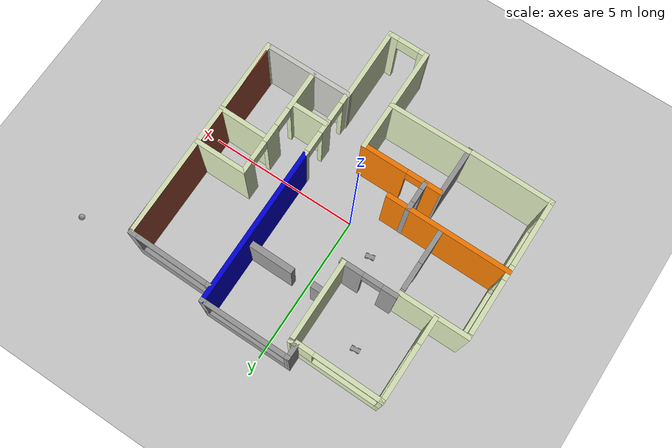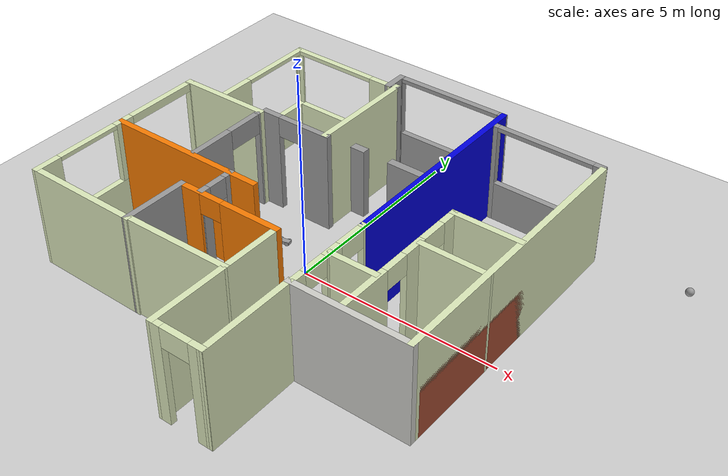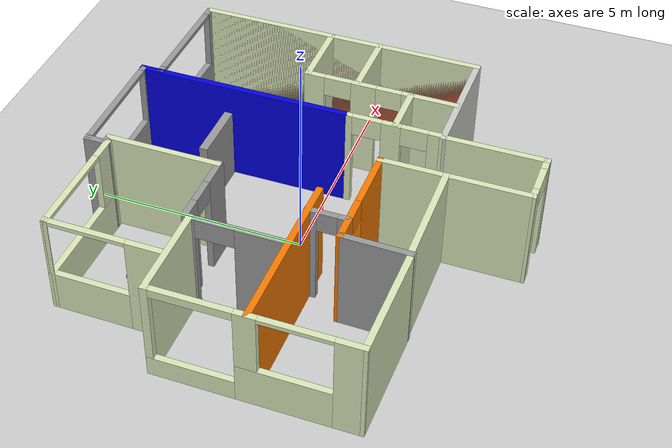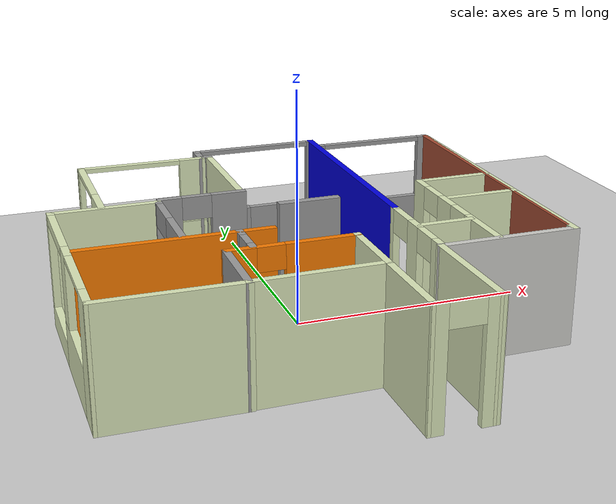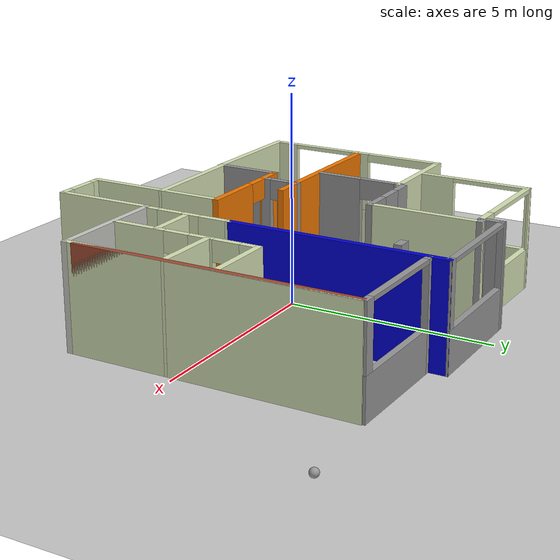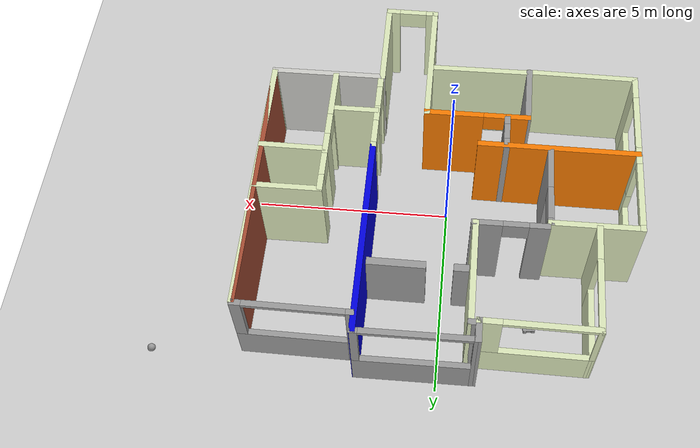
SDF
<sdf version="1.6">
 <world name="default">
  <plugin name="welcome_message" filename="libwelcome_message.so"/>
  <light name="sun" type="directional">
   <pose>0 0 10 0 -0 0</pose>
   <diffuse>0.8 0.8 0.8 1</diffuse>
   <specular>0.1 0.1 0.1 1</specular>
   <attenuation>
    <range>1000</range>
    <constant>0.9</constant>
    <linear>0.01</linear>
    <quadratic>0.001</quadratic>
   </attenuation>
   <direction>-0.5 0.5 -1</direction>
  </light>
  <model name="ground_plane">
   <static>1</static>
   <link name="link">
    <collision name="collision">
     <geometry><plane><normal>0 0 1</normal><size>100 100</size></plane></geometry>
     <surface><friction><ode><mu>100</mu><mu2>50</mu2></ode></friction></surface>
    </collision>
    <visual name="visual">
     <cast_shadows>0</cast_shadows>
     <geometry><plane><normal>0 0 1</normal><size>100 100</size></plane></geometry>
     <material>
      <script><uri>file://media/materials/scripts/gazebo.material</uri><name>Gazebo/Grey</name></script>
     </material>
    </visual>
   </link>
  </model>
  <gravity>0 0 -9.8</gravity>
  <magnetic_field>6e-06 2.3e-05 -4.2e-05</magnetic_field>
  <atmosphere type="adiabatic"/>
  <physics name="default_physics" default="0" type="ode">
   <max_step_size>0.001</max_step_size>
   <real_time_factor>1</real_time_factor>
   <real_time_update_rate>1000</real_time_update_rate>
  </physics>
  <scene><ambient>0.4 0.4 0.4 1</ambient><background>0.7 0.7 0.7 1</background><shadows>1</shadows></scene>
  <spherical_coordinates>
   <surface_model>EARTH_WGS84</surface_model>
   <latitude_deg>0</latitude_deg>
   <longitude_deg>0</longitude_deg>
   <elevation>0</elevation>
   <heading_deg>0</heading_deg>
  </spherical_coordinates>
  <model name="condo-2">
   <pose>0.03173 -0.150345 0 0 -0 0</pose>
   <link name="Wall_1">
    <collision name="Wall_1_Collision">
     <geometry><box><size>6.75 0.15 2.5</size></box></geometry>
     <pose>0 0 1.25 0 -0 0</pose>
    </collision>
    <visual name="Wall_1_Visual">
     <pose>0 0 1.25 0 -0 0</pose>
     <geometry><box><size>6.75 0.15 2.5</size></box></geometry>
     <material>
      <script><uri>file://media/materials/scripts/gazebo.material</uri><name>Gazebo/Bricks</name></script>
      <ambient>1 1 1 1</ambient>
     </material>
     <meta><layer>0</layer></meta>
    </visual>
    <pose>4.74151 1.02898 0 0 0 -1.5708</pose>
   </link>
   <link name="Wall_10">
    <collision name="Wall_10_Collision">
     <geometry><box><size>1.68411 0.15 2.5</size></box></geometry>
     <pose>0 0 1.25 0 -0 0</pose>
    </collision>
    <visual name="Wall_10_Visual">
     <pose>0 0 1.25 0 -0 0</pose>
     <geometry><box><size>1.68411 0.15 2.5</size></box></geometry>
     <material>
      <script><uri>file://media/materials/scripts/gazebo.material</uri><name>Gazebo/Grey</name></script>
      <ambient>1 1 1 1</ambient>
     </material>
     <meta><layer>0</layer></meta>
    </visual>
    <pose>-1.96752 -2.21739 0 0 0 -1.58289</pose>
   </link>
   <link name="Wall_11">
    <collision name="Wall_11_Collision">
     <geometry><box><size>2.91482 0.15 2.5</size></box></geometry>
     <pose>0 0 1.25 0 -0 0</pose>
    </collision>
    <visual name="Wall_11_Visual">
     <pose>0 0 1.25 0 -0 0</pose>
     <geometry><box><size>2.91482 0.15 2.5</size></box></geometry>
     <material>
      <script><uri>file://media/materials/scripts/gazebo.material</uri><name>Gazebo/Grey</name></script>
      <ambient>0.854902 0.901961 0.72549 1</ambient>
     </material>
     <meta><layer>0</layer></meta>
    </visual>
    <pose>-3.35881 -2.96461 0 0 -0 3.12724</pose>
   </link>
   <link name="Wall_12">
    <pose>-4.74082 -0.637006 0 0 -0 1.5708</pose>
    <visual name="Wall_12_Visual_0">
     <pose>-2.04278 0 1.25 0 -0 0</pose>
     <geometry><box><size>0.679963 0.15 2.5</size></box></geometry>
     <material>
      <script><uri>file://media/materials/scripts/gazebo.material</uri><name>Gazebo/Grey</name></script>
      <ambient>0.854902 0.901961 0.72549 1</ambient>
     </material>
     <meta><layer>0</layer></meta>
    </visual>
    <collision name="Wall_12_Collision_0">
     <geometry><box><size>0.679963 0.15 2.5</size></box></geometry>
     <pose>-2.04278 0 1.25 0 -0 0</pose>
    </collision>
    <visual name="Wall_12_Visual_1">
     <pose>-0.651319 0 0.5 0 -0 0</pose>
     <geometry><box><size>2.10296 0.15 1</size></box></geometry>
     <material>
      <script><uri>file://media/materials/scripts/gazebo.material</uri><name>Gazebo/Grey</name></script>
      <ambient>0.854902 0.901961 0.72549 1</ambient>
     </material>
     <meta><layer>0</layer></meta>
    </visual>
    <collision name="Wall_12_Collision_1">
     <geometry><box><size>2.10296 0.15 1</size></box></geometry>
     <pose>-0.651319 0 0.5 0 -0 0</pose>
    </collision>
    <visual name="Wall_12_Visual_2">
     <pose>1.39146 0 0.25 0 -0 0</pose>
     <geometry><box><size>1.9826 0.15 0.5</size></box></geometry>
     <material>
      <script><uri>file://media/materials/scripts/gazebo.material</uri><name>Gazebo/Grey</name></script>
      <ambient>0.854902 0.901961 0.72549 1</ambient>
     </material>
     <meta><layer>0</layer></meta>
    </visual>
    <collision name="Wall_12_Collision_2">
     <geometry><box><size>1.9826 0.15 0.5</size></box></geometry>
     <pose>1.39146 0 0.25 0 -0 0</pose>
    </collision>
    <visual name="Wall_12_Visual_3">
     <pose>2.29396 0 1.5 0 -0 0</pose>
     <geometry><box><size>0.1776 0.15 2</size></box></geometry>
     <material>
      <script><uri>file://media/materials/scripts/gazebo.material</uri><name>Gazebo/Grey</name></script>
      <ambient>0.854902 0.901961 0.72549 1</ambient>
     </material>
     <meta><layer>0</layer></meta>
    </visual>
    <collision name="Wall_12_Collision_3">
     <geometry><box><size>0.1776 0.15 2</size></box></geometry>
     <pose>2.29396 0 1.5 0 -0 0</pose>
    </collision>
    <visual name="Wall_12_Visual_4">
     <pose>0.152181 0 1.75 0 -0 0</pose>
     <geometry><box><size>0.495963 0.15 1.5</size></box></geometry>
     <material>
      <script><uri>file://media/materials/scripts/gazebo.material</uri><name>Gazebo/Grey</name></script>
      <ambient>0.854902 0.901961 0.72549 1</ambient>
     </material>
     <meta><layer>0</layer></meta>
    </visual>
    <collision name="Wall_12_Collision_4">
     <geometry><box><size>0.495963 0.15 1.5</size></box></geometry>
     <pose>0.152181 0 1.75 0 -0 0</pose>
    </collision>
    <visual name="Wall_12_Visual_5">
     <pose>1.30266 0 2.4 0 -0 0</pose>
     <geometry><box><size>1.805 0.15 0.2</size></box></geometry>
     <material>
      <script><uri>file://media/materials/scripts/gazebo.material</uri><name>Gazebo/Grey</name></script>
      <ambient>0.854902 0.901961 0.72549 1</ambient>
     </material>
     <meta><layer>0</layer></meta>
    </visual>
    <collision name="Wall_12_Collision_5">
     <geometry><box><size>1.805 0.15 0.2</size></box></geometry>
     <pose>1.30266 0 2.4 0 -0 0</pose>
    </collision>
    <visual name="Wall_12_Visual_6">
     <pose>-0.8993 0 2.45 0 -0 0</pose>
     <geometry><box><size>1.607 0.15 0.1</size></box></geometry>
     <material>
      <script><uri>file://media/materials/scripts/gazebo.material</uri><name>Gazebo/Grey</name></script>
      <ambient>0.854902 0.901961 0.72549 1</ambient>
     </material>
     <meta><layer>0</layer></meta>
    </visual>
    <collision name="Wall_12_Collision_6">
     <geometry><box><size>1.607 0.15 0.1</size></box></geometry>
     <pose>-0.8993 0 2.45 0 -0 0</pose>
    </collision>
   </link>
   <link name="Wall_13">
    <collision name="Wall_13_Collision">
     <geometry><box><size>2.34535 0.15 2.5</size></box></geometry>
     <pose>0 0 1.25 0 -0 0</pose>
    </collision>
    <visual name="Wall_13_Visual">
     <pose>0 0 1.25 0 -0 0</pose>
     <geometry><box><size>2.34535 0.15 2.5</size></box></geometry>
     <material>
      <script><uri>file://media/materials/scripts/gazebo.material</uri><name>Gazebo/Grey</name></script>
      <ambient>0.854902 0.901961 0.72549 1</ambient>
     </material>
     <meta><layer>0</layer></meta>
    </visual>
    <pose>-3.64314 1.67076 0 0 -0 0</pose>
   </link>
   <link name="Wall_15">
    <collision name="Wall_15_Collision">
     <geometry><box><size>2.75533 0.15 2.5</size></box></geometry>
     <pose>0 0 1.25 0 -0 0</pose>
    </collision>
    <visual name="Wall_15_Visual">
     <pose>0 0 1.25 0 -0 0</pose>
     <geometry><box><size>2.75533 0.15 2.5</size></box></geometry>
     <material>
      <script><uri>file://media/materials/scripts/gazebo.material</uri><name>Gazebo/Grey</name></script>
      <ambient>0.854902 0.901961 0.72549 1</ambient>
     </material>
     <meta><layer>0</layer></meta>
    </visual>
    <pose>-0.660906 -2.95138 0 0 0 -3.13652</pose>
   </link>
   <link name="Wall_17">
    <collision name="Wall_17_Collision">
     <geometry><box><size>4.10436 0.15 2.5</size></box></geometry>
     <pose>0 0 1.25 0 -0 0</pose>
    </collision>
    <visual name="Wall_17_Visual">
     <pose>0 0 1.25 0 -0 0</pose>
     <geometry><box><size>4.10436 0.15 2.5</size></box></geometry>
     <material>
      <script><uri>file://media/materials/scripts/gazebo.material</uri><name>Gazebo/Grey</name></script>
      <ambient>0.960784 0.478431 0 1</ambient>
     </material>
     <meta><layer>0</layer></meta>
    </visual>
    <pose>-2.75046 -0.537818 0 0 0 -0.006689</pose>
   </link>
   <link name="Wall_20">
    <pose>-3.70266 3.08583 0 0 -0 1.56589</pose>
    <visual name="Wall_20_Visual_0">
     <pose>-0.964016 0 1.25 0 -0 0</pose>
     <geometry><box><size>0.9199 0.15 2.5</size></box></geometry>
     <material>
      <script><uri>file://media/materials/scripts/gazebo.material</uri><name>Gazebo/Grey</name></script>
      <ambient>0.854902 0.901961 0.72549 1</ambient>
     </material>
     <meta><layer>0</layer></meta>
    </visual>
    <collision name="Wall_20_Collision_0">
     <geometry><box><size>0.9199 0.15 2.5</size></box></geometry>
     <pose>-0.964016 0 1.25 0 -0 0</pose>
    </collision>
    <visual name="Wall_20_Visual_1">
     <pose>0.45995 0 0.5 0 -0 0</pose>
     <geometry><box><size>1.92803 0.15 1</size></box></geometry>
     <material>
      <script><uri>file://media/materials/scripts/gazebo.material</uri><name>Gazebo/Grey</name></script>
      <ambient>0.854902 0.901961 0.72549 1</ambient>
     </material>
     <meta><layer>0</layer></meta>
    </visual>
    <collision name="Wall_20_Collision_1">
     <geometry><box><size>1.92803 0.15 1</size></box></geometry>
     <pose>0.45995 0 0.5 0 -0 0</pose>
    </collision>
    <visual name="Wall_20_Visual_2">
     <pose>1.39995 0 1.75 0 -0 0</pose>
     <geometry><box><size>0.048033 0.15 1.5</size></box></geometry>
     <material>
      <script><uri>file://media/materials/scripts/gazebo.material</uri><name>Gazebo/Grey</name></script>
      <ambient>0.854902 0.901961 0.72549 1</ambient>
     </material>
     <meta><layer>0</layer></meta>
    </visual>
    <collision name="Wall_20_Collision_2">
     <geometry><box><size>0.048033 0.15 1.5</size></box></geometry>
     <pose>1.39995 0 1.75 0 -0 0</pose>
    </collision>
    <visual name="Wall_20_Visual_3">
     <pose>0.435934 0 2.45 0 -0 0</pose>
     <geometry><box><size>1.88 0.15 0.1</size></box></geometry>
     <material>
      <script><uri>file://media/materials/scripts/gazebo.material</uri><name>Gazebo/Grey</name></script>
      <ambient>0.854902 0.901961 0.72549 1</ambient>
     </material>
     <meta><layer>0</layer></meta>
    </visual>
    <collision name="Wall_20_Collision_3">
     <geometry><box><size>1.88 0.15 0.1</size></box></geometry>
     <pose>0.435934 0 2.45 0 -0 0</pose>
    </collision>
   </link>
   <link name="Wall_21">
    <pose>-2.31403 4.41494 0 0 0 -0.014353</pose>
    <visual name="Wall_21_Visual_0">
     <pose>-1.44711 0 1.25 0 -0 0</pose>
     <geometry><box><size>0.020096 0.15 2.5</size></box></geometry>
     <material>
      <script><uri>file://media/materials/scripts/gazebo.material</uri><name>Gazebo/Grey</name></script>
      <ambient>0.854902 0.901961 0.72549 1</ambient>
     </material>
     <meta><layer>0</layer></meta>
    </visual>
    <collision name="Wall_21_Collision_0">
     <geometry><box><size>0.020096 0.15 2.5</size></box></geometry>
     <pose>-1.44711 0 1.25 0 -0 0</pose>
    </collision>
    <visual name="Wall_21_Visual_1">
     <pose>0.010048 0 0.5 0 -0 0</pose>
     <geometry><box><size>2.89421 0.15 1</size></box></geometry>
     <material>
      <script><uri>file://media/materials/scripts/gazebo.material</uri><name>Gazebo/Grey</name></script>
      <ambient>0.854902 0.901961 0.72549 1</ambient>
     </material>
     <meta><layer>0</layer></meta>
    </visual>
    <collision name="Wall_21_Collision_1">
     <geometry><box><size>2.89421 0.15 1</size></box></geometry>
     <pose>0.010048 0 0.5 0 -0 0</pose>
    </collision>
    <visual name="Wall_21_Visual_2">
     <pose>1.15505 0 1.75 0 -0 0</pose>
     <geometry><box><size>0.604214 0.15 1.5</size></box></geometry>
     <material>
      <script><uri>file://media/materials/scripts/gazebo.material</uri><name>Gazebo/Grey</name></script>
      <ambient>0.854902 0.901961 0.72549 1</ambient>
     </material>
     <meta><layer>0</layer></meta>
    </visual>
    <collision name="Wall_21_Collision_2">
     <geometry><box><size>0.604214 0.15 1.5</size></box></geometry>
     <pose>1.15505 0 1.75 0 -0 0</pose>
    </collision>
    <visual name="Wall_21_Visual_3">
     <pose>-0.292059 0 2.45 0 -0 0</pose>
     <geometry><box><size>2.29 0.15 0.1</size></box></geometry>
     <material>
      <script><uri>file://media/materials/scripts/gazebo.material</uri><name>Gazebo/Grey</name></script>
      <ambient>0.854902 0.901961 0.72549 1</ambient>
     </material>
     <meta><layer>0</layer></meta>
    </visual>
    <collision name="Wall_21_Collision_3">
     <geometry><box><size>2.29 0.15 0.1</size></box></geometry>
     <pose>-0.292059 0 2.45 0 -0 0</pose>
    </collision>
   </link>
   <link name="Wall_22">
    <collision name="Wall_22_Collision">
     <geometry><box><size>0.6261 0.15 2.5</size></box></geometry>
     <pose>0 0 1.25 0 -0 0</pose>
    </collision>
    <visual name="Wall_22_Visual">
     <pose>0 0 1.25 0 -0 0</pose>
     <geometry><box><size>0.6261 0.15 2.5</size></box></geometry>
     <material>
      <script><uri>file://media/materials/scripts/gazebo.material</uri><name>Gazebo/Grey</name></script>
      <ambient>1 1 1 1</ambient>
     </material>
     <meta><layer>0</layer></meta>
    </visual>
    <pose>-0.932018 4.63316 0 0 -0 1.5708</pose>
   </link>
   <link name="Wall_23">
    <pose>0.492994 4.87136 0 0 -0 0.000105</pose>
    <visual name="Wall_23_Visual_0">
     <pose>-1.41577 0 1.25 0 -0 0</pose>
     <geometry><box><size>0.168462 0.15 2.5</size></box></geometry>
     <material>
      <script><uri>file://media/materials/scripts/gazebo.material</uri><name>Gazebo/Grey</name></script>
      <ambient>1 1 1 1</ambient>
     </material>
     <meta><layer>0</layer></meta>
    </visual>
    <collision name="Wall_23_Collision_0">
     <geometry><box><size>0.168462 0.15 2.5</size></box></geometry>
     <pose>-1.41577 0 1.25 0 -0 0</pose>
    </collision>
    <visual name="Wall_23_Visual_1">
     <pose>0.084231 0 0.5 0 -0 0</pose>
     <geometry><box><size>2.83154 0.15 1</size></box></geometry>
     <material>
      <script><uri>file://media/materials/scripts/gazebo.material</uri><name>Gazebo/Grey</name></script>
      <ambient>1 1 1 1</ambient>
     </material>
     <meta><layer>0</layer></meta>
    </visual>
    <collision name="Wall_23_Collision_1">
     <geometry><box><size>2.83154 0.15 1</size></box></geometry>
     <pose>0.084231 0 0.5 0 -0 0</pose>
    </collision>
    <visual name="Wall_23_Visual_2">
     <pose>1.39923 0 1.75 0 -0 0</pose>
     <geometry><box><size>0.201538 0.15 1.5</size></box></geometry>
     <material>
      <script><uri>file://media/materials/scripts/gazebo.material</uri><name>Gazebo/Grey</name></script>
      <ambient>1 1 1 1</ambient>
     </material>
     <meta><layer>0</layer></meta>
    </visual>
    <collision name="Wall_23_Collision_2">
     <geometry><box><size>0.201538 0.15 1.5</size></box></geometry>
     <pose>1.39923 0 1.75 0 -0 0</pose>
    </collision>
    <visual name="Wall_23_Visual_3">
     <pose>-0.016538 0 2.45 0 -0 0</pose>
     <geometry><box><size>2.63 0.15 0.1</size></box></geometry>
     <material>
      <script><uri>file://media/materials/scripts/gazebo.material</uri><name>Gazebo/Grey</name></script>
      <ambient>1 1 1 1</ambient>
     </material>
     <meta><layer>0</layer></meta>
    </visual>
    <collision name="Wall_23_Collision_3">
     <geometry><box><size>2.63 0.15 0.1</size></box></geometry>
     <pose>-0.016538 0 2.45 0 -0 0</pose>
    </collision>
   </link>
   <link name="Wall_24">
    <collision name="Wall_24_Collision">
     <geometry><box><size>5.25485 0.15 2.5</size></box></geometry>
     <pose>0 0 1.25 0 -0 0</pose>
    </collision>
    <visual name="Wall_24_Visual">
     <pose>0 0 1.25 0 -0 0</pose>
     <geometry><box><size>5.25485 0.15 2.5</size></box></geometry>
     <material>
      <script><uri>file://media/materials/scripts/gazebo.material</uri><name>Gazebo/Grey</name></script>
      <ambient>0 0 0.866667 1</ambient>
     </material>
     <meta><layer>0</layer></meta>
    </visual>
    <pose>1.92151 2.31901 0 0 0 -1.56943</pose>
   </link>
   <link name="Wall_28">
    <pose>1.92458 -1.35359 0 0 0 -1.5708</pose>
    <visual name="Wall_28_Visual_0">
     <pose>-1.04991 0 1.25 0 -0 0</pose>
     <geometry><box><size>0.150175 0.15 2.5</size></box></geometry>
     <material>
      <script><uri>file://media/materials/scripts/gazebo.material</uri><name>Gazebo/Grey</name></script>
      <ambient>0.854902 0.901961 0.72549 1</ambient>
     </material>
     <meta><layer>0</layer></meta>
    </visual>
    <collision name="Wall_28_Collision_0">
     <geometry><box><size>0.150175 0.15 2.5</size></box></geometry>
     <pose>-1.04991 0 1.25 0 -0 0</pose>
    </collision>
    <visual name="Wall_28_Visual_1">
     <pose>-0.055337 0 1.25 0 -0 0</pose>
     <geometry><box><size>0.462175 0.15 2.5</size></box></geometry>
     <material>
      <script><uri>file://media/materials/scripts/gazebo.material</uri><name>Gazebo/Grey</name></script>
      <ambient>0.854902 0.901961 0.72549 1</ambient>
     </material>
     <meta><layer>0</layer></meta>
    </visual>
    <collision name="Wall_28_Collision_1">
     <geometry><box><size>0.462175 0.15 2.5</size></box></geometry>
     <pose>-0.055337 0 1.25 0 -0 0</pose>
    </collision>
    <visual name="Wall_28_Visual_2">
     <pose>0.968125 0 1.25 0 -0 0</pose>
     <geometry><box><size>0.31375 0.15 2.5</size></box></geometry>
     <material>
      <script><uri>file://media/materials/scripts/gazebo.material</uri><name>Gazebo/Grey</name></script>
      <ambient>0.854902 0.901961 0.72549 1</ambient>
     </material>
     <meta><layer>0</layer></meta>
    </visual>
    <collision name="Wall_28_Collision_2">
     <geometry><box><size>0.31375 0.15 2.5</size></box></geometry>
     <pose>0.968125 0 1.25 0 -0 0</pose>
    </collision>
    <visual name="Wall_28_Visual_3">
     <pose>-0.630625 0 2.25 0 -0 0</pose>
     <geometry><box><size>0.6884 0.15 0.5</size></box></geometry>
     <material>
      <script><uri>file://media/materials/scripts/gazebo.material</uri><name>Gazebo/Grey</name></script>
      <ambient>0.854902 0.901961 0.72549 1</ambient>
     </material>
     <meta><layer>0</layer></meta>
    </visual>
    <collision name="Wall_28_Collision_3">
     <geometry><box><size>0.6884 0.15 0.5</size></box></geometry>
     <pose>-0.630625 0 2.25 0 -0 0</pose>
    </collision>
    <visual name="Wall_28_Visual_4">
     <pose>0.4935 0 2.25 0 -0 0</pose>
     <geometry><box><size>0.6355 0.15 0.5</size></box></geometry>
     <material>
      <script><uri>file://media/materials/scripts/gazebo.material</uri><name>Gazebo/Grey</name></script>
      <ambient>0.854902 0.901961 0.72549 1</ambient>
     </material>
     <meta><layer>0</layer></meta>
    </visual>
    <collision name="Wall_28_Collision_4">
     <geometry><box><size>0.6355 0.15 0.5</size></box></geometry>
     <pose>0.4935 0 2.25 0 -0 0</pose>
    </collision>
   </link>
   <link name="Wall_3">
    <collision name="Wall_3_Collision">
     <geometry><box><size>7 0.15 2.5</size></box></geometry>
     <pose>0 0 1.25 0 -0 0</pose>
    </collision>
    <visual name="Wall_3_Visual">
     <pose>0 0 1.25 0 -0 0</pose>
     <geometry><box><size>7 0.15 2.5</size></box></geometry>
     <material>
      <script><uri>file://media/materials/scripts/gazebo.material</uri><name>Gazebo/Grey</name></script>
      <ambient>0.854902 0.901961 0.72549 1</ambient>
     </material>
     <meta><layer>0</layer></meta>
    </visual>
    <pose>4.74151 0.903982 0 0 0 -1.5708</pose>
   </link>
   <link name="Wall_31">
    <pose>3.34627 4.41494 0 0 0 -0.014492</pose>
    <visual name="Wall_31_Visual_0">
     <pose>-1.34195 0 1.25 0 -0 0</pose>
     <geometry><box><size>0.203956 0.15 2.5</size></box></geometry>
     <material>
      <script><uri>file://media/materials/scripts/gazebo.material</uri><name>Gazebo/Grey</name></script>
      <ambient>1 1 1 1</ambient>
     </material>
     <meta><layer>0</layer></meta>
    </visual>
    <collision name="Wall_31_Collision_0">
     <geometry><box><size>0.203956 0.15 2.5</size></box></geometry>
     <pose>-1.34195 0 1.25 0 -0 0</pose>
    </collision>
    <visual name="Wall_31_Visual_1">
     <pose>0.101978 0 0.5 0 -0 0</pose>
     <geometry><box><size>2.68391 0.15 1</size></box></geometry>
     <material>
      <script><uri>file://media/materials/scripts/gazebo.material</uri><name>Gazebo/Grey</name></script>
      <ambient>1 1 1 1</ambient>
     </material>
     <meta><layer>0</layer></meta>
    </visual>
    <collision name="Wall_31_Collision_1">
     <geometry><box><size>2.68391 0.15 1</size></box></geometry>
     <pose>0.101978 0 0.5 0 -0 0</pose>
    </collision>
    <visual name="Wall_31_Visual_2">
     <pose>1.30698 0 1.75 0 -0 0</pose>
     <geometry><box><size>0.273907 0.15 1.5</size></box></geometry>
     <material>
      <script><uri>file://media/materials/scripts/gazebo.material</uri><name>Gazebo/Grey</name></script>
      <ambient>1 1 1 1</ambient>
     </material>
     <meta><layer>0</layer></meta>
    </visual>
    <collision name="Wall_31_Collision_2">
     <geometry><box><size>0.273907 0.15 1.5</size></box></geometry>
     <pose>1.30698 0 1.75 0 -0 0</pose>
    </collision>
    <visual name="Wall_31_Visual_3">
     <pose>-0.034975 0 2.45 0 -0 0</pose>
     <geometry><box><size>2.41 0.15 0.1</size></box></geometry>
     <material>
      <script><uri>file://media/materials/scripts/gazebo.material</uri><name>Gazebo/Grey</name></script>
      <ambient>1 1 1 1</ambient>
     </material>
     <meta><layer>0</layer></meta>
    </visual>
    <collision name="Wall_31_Collision_3">
     <geometry><box><size>2.41 0.15 0.1</size></box></geometry>
     <pose>-0.034975 0 2.45 0 -0 0</pose>
    </collision>
   </link>
   <link name="Wall_33">
    <collision name="Wall_33_Collision">
     <geometry><box><size>1.25 0.15 2.5</size></box></geometry>
     <pose>0 0 1.25 0 -0 0</pose>
    </collision>
    <visual name="Wall_33_Visual">
     <pose>0 0 1.25 0 -0 0</pose>
     <geometry><box><size>1.25 0.15 2.5</size></box></geometry>
     <material>
      <script><uri>file://media/materials/scripts/gazebo.material</uri><name>Gazebo/Grey</name></script>
      <ambient>0.854902 0.901961 0.72549 1</ambient>
     </material>
     <meta><layer>0</layer></meta>
    </visual>
    <pose>2.51426 -1.38422 0 0 -0 0</pose>
   </link>
   <link name="Wall_4">
    <collision name="Wall_4_Collision">
     <geometry><box><size>3 0.15 2.5</size></box></geometry>
     <pose>0 0 1.25 0 -0 0</pose>
    </collision>
    <visual name="Wall_4_Visual">
     <pose>0 0 1.25 0 -0 0</pose>
     <geometry><box><size>3 0.15 2.5</size></box></geometry>
     <material>
      <script><uri>file://media/materials/scripts/gazebo.material</uri><name>Gazebo/CeilingTiled</name></script>
      <ambient>1 1 1 1</ambient>
     </material>
     <meta><layer>0</layer></meta>
    </visual>
    <pose>3.31651 -2.52102 0 0 -0 3.14159</pose>
   </link>
   <link name="Wall_43">
    <pose>3.11483 -0.655443 0 0 -0 1.5708</pose>
    <visual name="Wall_43_Visual_0">
     <pose>-1.19296 0 1.25 0 -0 0</pose>
     <geometry><box><size>1.36409 0.15 2.5</size></box></geometry>
     <material>
      <script><uri>file://media/materials/scripts/gazebo.material</uri><name>Gazebo/Grey</name></script>
      <ambient>0.854902 0.901961 0.72549 1</ambient>
     </material>
     <meta><layer>0</layer></meta>
    </visual>
    <collision name="Wall_43_Collision_0">
     <geometry><box><size>1.36409 0.15 2.5</size></box></geometry>
     <pose>-1.19296 0 1.25 0 -0 0</pose>
    </collision>
    <visual name="Wall_43_Visual_1">
     <pose>0.415188 0 1.25 0 -0 0</pose>
     <geometry><box><size>0.60765 0.15 2.5</size></box></geometry>
     <material>
      <script><uri>file://media/materials/scripts/gazebo.material</uri><name>Gazebo/Grey</name></script>
      <ambient>0.854902 0.901961 0.72549 1</ambient>
     </material>
     <meta><layer>0</layer></meta>
    </visual>
    <collision name="Wall_43_Collision_1">
     <geometry><box><size>0.60765 0.15 2.5</size></box></geometry>
     <pose>0.415188 0 1.25 0 -0 0</pose>
    </collision>
    <visual name="Wall_43_Visual_2">
     <pose>1.62798 0 1.25 0 -0 0</pose>
     <geometry><box><size>0.494037 0.15 2.5</size></box></geometry>
     <material>
      <script><uri>file://media/materials/scripts/gazebo.material</uri><name>Gazebo/Grey</name></script>
      <ambient>0.854902 0.901961 0.72549 1</ambient>
     </material>
     <meta><layer>0</layer></meta>
    </visual>
    <collision name="Wall_43_Collision_2">
     <geometry><box><size>0.494037 0.15 2.5</size></box></geometry>
     <pose>1.62798 0 1.25 0 -0 0</pose>
    </collision>
    <visual name="Wall_43_Visual_3">
     <pose>-0.199775 0 2.25 0 -0 0</pose>
     <geometry><box><size>0.622275 0.15 0.5</size></box></geometry>
     <material>
      <script><uri>file://media/materials/scripts/gazebo.material</uri><name>Gazebo/Grey</name></script>
      <ambient>0.854902 0.901961 0.72549 1</ambient>
     </material>
     <meta><layer>0</layer></meta>
    </visual>
    <collision name="Wall_43_Collision_3">
     <geometry><box><size>0.622275 0.15 0.5</size></box></geometry>
     <pose>-0.199775 0 2.25 0 -0 0</pose>
    </collision>
    <visual name="Wall_43_Visual_4">
     <pose>1.04999 0 2.25 0 -0 0</pose>
     <geometry><box><size>0.66195 0.15 0.5</size></box></geometry>
     <material>
      <script><uri>file://media/materials/scripts/gazebo.material</uri><name>Gazebo/Grey</name></script>
      <ambient>0.854902 0.901961 0.72549 1</ambient>
     </material>
     <meta><layer>0</layer></meta>
    </visual>
    <collision name="Wall_43_Collision_4">
     <geometry><box><size>0.66195 0.15 0.5</size></box></geometry>
     <pose>1.04999 0 2.25 0 -0 0</pose>
    </collision>
   </link>
   <link name="Wall_44">
    <collision name="Wall_44_Collision">
     <geometry><box><size>1.75 0.15 2.5</size></box></geometry>
     <pose>0 0 1.25 0 -0 0</pose>
    </collision>
    <visual name="Wall_44_Visual">
     <pose>0 0 1.25 0 -0 0</pose>
     <geometry><box><size>1.75 0.15 2.5</size></box></geometry>
     <material>
      <script><uri>file://media/materials/scripts/gazebo.material</uri><name>Gazebo/Grey</name></script>
      <ambient>0.854902 0.901961 0.72549 1</ambient>
     </material>
     <meta><layer>0</layer></meta>
    </visual>
    <pose>3.91483 1.14456 0 0 -0 0</pose>
   </link>
   <link name="Wall_46">
    <collision name="Wall_46_Collision">
     <geometry><box><size>1.71061 0.15 2.5</size></box></geometry>
     <pose>0 0 1.25 0 -0 0</pose>
    </collision>
    <visual name="Wall_46_Visual">
     <pose>0 0 1.25 0 -0 0</pose>
     <geometry><box><size>1.71061 0.15 2.5</size></box></geometry>
     <material>
      <script><uri>file://media/materials/scripts/gazebo.material</uri><name>Gazebo/Grey</name></script>
      <ambient>0.854902 0.901961 0.72549 1</ambient>
     </material>
     <meta><layer>0</layer></meta>
    </visual>
    <pose>3.96123 -0.081556 0 0 0 -0.008474</pose>
   </link>
   <link name="Wall_48">
    <pose>-1.43457 -0.962818 0 0 0 -1.5708</pose>
    <visual name="Wall_48_Visual_0">
     <pose>-0.353569 0 1.25 0 -0 0</pose>
     <geometry><box><size>0.292862 0.15 2.5</size></box></geometry>
     <material>
      <script><uri>file://media/materials/scripts/gazebo.material</uri><name>Gazebo/Grey</name></script>
      <ambient>1 1 1 1</ambient>
     </material>
     <meta><layer>0</layer></meta>
    </visual>
    <collision name="Wall_48_Collision_0">
     <geometry><box><size>0.292862 0.15 2.5</size></box></geometry>
     <pose>-0.353569 0 1.25 0 -0 0</pose>
    </collision>
    <visual name="Wall_48_Visual_1">
     <pose>0.378219 0 1.25 0 -0 0</pose>
     <geometry><box><size>0.243563 0.15 2.5</size></box></geometry>
     <material>
      <script><uri>file://media/materials/scripts/gazebo.material</uri><name>Gazebo/Grey</name></script>
      <ambient>1 1 1 1</ambient>
     </material>
     <meta><layer>0</layer></meta>
    </visual>
    <collision name="Wall_48_Collision_1">
     <geometry><box><size>0.243563 0.15 2.5</size></box></geometry>
     <pose>0.378219 0 1.25 0 -0 0</pose>
    </collision>
    <visual name="Wall_48_Visual_2">
     <pose>0.02465 0 2.25 0 -0 0</pose>
     <geometry><box><size>0.463575 0.15 0.5</size></box></geometry>
     <material>
      <script><uri>file://media/materials/scripts/gazebo.material</uri><name>Gazebo/Grey</name></script>
      <ambient>1 1 1 1</ambient>
     </material>
     <meta><layer>0</layer></meta>
    </visual>
    <collision name="Wall_48_Collision_2">
     <geometry><box><size>0.463575 0.15 0.5</size></box></geometry>
     <pose>0.02465 0 2.25 0 -0 0</pose>
    </collision>
   </link>
   <link name="Wall_5">
    <collision name="Wall_5_Collision">
     <geometry><box><size>2.5 0.15 2.5</size></box></geometry>
     <pose>0 0 1.25 0 -0 0</pose>
    </collision>
    <visual name="Wall_5_Visual">
     <pose>0 0 1.25 0 -0 0</pose>
     <geometry><box><size>2.5 0.15 2.5</size></box></geometry>
     <material>
      <script><uri>file://media/materials/scripts/gazebo.material</uri><name>Gazebo/Grey</name></script>
      <ambient>0.854902 0.901961 0.72549 1</ambient>
     </material>
     <meta><layer>0</layer></meta>
    </visual>
    <pose>1.89812 -3.69602 0 0 0 -1.56517</pose>
   </link>
   <link name="Wall_50">
    <pose>-2.54547 0.620757 0 0 0 -1.5708</pose>
    <visual name="Wall_50_Visual_0">
     <pose>-1.02155 0 1.25 0 -0 0</pose>
     <geometry><box><size>0.2069 0.15 2.5</size></box></geometry>
     <material>
      <script><uri>file://media/materials/scripts/gazebo.material</uri><name>Gazebo/Grey</name></script>
      <ambient>1 1 1 1</ambient>
     </material>
     <meta><layer>0</layer></meta>
    </visual>
    <collision name="Wall_50_Collision_0">
     <geometry><box><size>0.2069 0.15 2.5</size></box></geometry>
     <pose>-1.02155 0 1.25 0 -0 0</pose>
    </collision>
    <visual name="Wall_50_Visual_1">
     <pose>0.55345 0 1.25 0 -0 0</pose>
     <geometry><box><size>1.1431 0.15 2.5</size></box></geometry>
     <material>
      <script><uri>file://media/materials/scripts/gazebo.material</uri><name>Gazebo/Grey</name></script>
      <ambient>1 1 1 1</ambient>
     </material>
     <meta><layer>0</layer></meta>
    </visual>
    <collision name="Wall_50_Collision_1">
     <geometry><box><size>1.1431 0.15 2.5</size></box></geometry>
     <pose>0.55345 0 1.25 0 -0 0</pose>
    </collision>
    <visual name="Wall_50_Visual_2">
     <pose>-0.4681 0 2.25 0 -0 0</pose>
     <geometry><box><size>0.9 0.15 0.5</size></box></geometry>
     <material>
      <script><uri>file://media/materials/scripts/gazebo.material</uri><name>Gazebo/Grey</name></script>
      <ambient>1 1 1 1</ambient>
     </material>
     <meta><layer>0</layer></meta>
    </visual>
    <collision name="Wall_50_Collision_2">
     <geometry><box><size>0.9 0.15 0.5</size></box></geometry>
     <pose>-0.4681 0 2.25 0 -0 0</pose>
    </collision>
   </link>
   <link name="Wall_53">
    <collision name="Wall_53_Collision">
     <geometry><box><size>2.795 0.15 2.5</size></box></geometry>
     <pose>0 0 1.25 0 -0 0</pose>
    </collision>
    <visual name="Wall_53_Visual">
     <pose>0 0 1.25 0 -0 0</pose>
     <geometry><box><size>2.795 0.15 2.5</size></box></geometry>
     <material>
      <script><uri>file://media/materials/scripts/gazebo.material</uri><name>Gazebo/Grey</name></script>
      <ambient>0.854902 0.901961 0.72549 1</ambient>
     </material>
     <meta><layer>0</layer></meta>
    </visual>
    <pose>-0.746868 3.12551 0 0 -0 1.5708</pose>
   </link>
   <link name="Wall_54">
    <collision name="Wall_54_Collision">
     <geometry><box><size>0.256623 0.15 2.5</size></box></geometry>
     <pose>0 0 1.25 0 -0 0</pose>
    </collision>
    <visual name="Wall_54_Visual">
     <pose>0 0 1.25 0 -0 0</pose>
     <geometry><box><size>0.256623 0.15 2.5</size></box></geometry>
     <material>
      <script><uri>file://media/materials/scripts/gazebo.material</uri><name>Gazebo/Grey</name></script>
      <ambient>1 1 1 1</ambient>
     </material>
     <meta><layer>0</layer></meta>
    </visual>
    <pose>-0.799768 4.44801 0 0 -0 3.14159</pose>
   </link>
   <link name="Wall_56">
    <pose>-1.58666 1.78978 0 0 -0 3.14159</pose>
    <visual name="Wall_56_Visual_0">
     <pose>-0.573337 0 1.25 0 -0 0</pose>
     <geometry><box><size>0.762449 0.15 2.5</size></box></geometry>
     <material>
      <script><uri>file://media/materials/scripts/gazebo.material</uri><name>Gazebo/Grey</name></script>
      <ambient>1 1 1 1</ambient>
     </material>
     <meta><layer>0</layer></meta>
    </visual>
    <collision name="Wall_56_Collision_0">
     <geometry><box><size>0.762449 0.15 2.5</size></box></geometry>
     <pose>-0.573337 0 1.25 0 -0 0</pose>
    </collision>
    <visual name="Wall_56_Visual_1">
     <pose>0.698975 0 1.25 0 -0 0</pose>
     <geometry><box><size>0.511174 0.15 2.5</size></box></geometry>
     <material>
      <script><uri>file://media/materials/scripts/gazebo.material</uri><name>Gazebo/Grey</name></script>
      <ambient>1 1 1 1</ambient>
     </material>
     <meta><layer>0</layer></meta>
    </visual>
    <collision name="Wall_56_Collision_1">
     <geometry><box><size>0.511174 0.15 2.5</size></box></geometry>
     <pose>0.698975 0 1.25 0 -0 0</pose>
    </collision>
    <visual name="Wall_56_Visual_2">
     <pose>0.125638 0 2.25 0 -0 0</pose>
     <geometry><box><size>0.6355 0.15 0.5</size></box></geometry>
     <material>
      <script><uri>file://media/materials/scripts/gazebo.material</uri><name>Gazebo/Grey</name></script>
      <ambient>1 1 1 1</ambient>
     </material>
     <meta><layer>0</layer></meta>
    </visual>
    <collision name="Wall_56_Collision_2">
     <geometry><box><size>0.6355 0.15 0.5</size></box></geometry>
     <pose>0.125638 0 2.25 0 -0 0</pose>
    </collision>
   </link>
   <link name="Wall_6">
    <pose>1.26663 -4.86671 0 0 -0 3.13469</pose>
    <visual name="Wall_6_Visual_0">
     <pose>-0.520222 0 1.25 0 -0 0</pose>
     <geometry><box><size>0.359336 0.15 2.5</size></box></geometry>
     <material>
      <script><uri>file://media/materials/scripts/gazebo.material</uri><name>Gazebo/Grey</name></script>
      <ambient>0.854902 0.901961 0.72549 1</ambient>
     </material>
     <meta><layer>0</layer></meta>
    </visual>
    <collision name="Wall_6_Collision_0">
     <geometry><box><size>0.359336 0.15 2.5</size></box></geometry>
     <pose>-0.520222 0 1.25 0 -0 0</pose>
    </collision>
    <visual name="Wall_6_Visual_1">
     <pose>0.53705 0 1.25 0 -0 0</pose>
     <geometry><box><size>0.32568 0.15 2.5</size></box></geometry>
     <material>
      <script><uri>file://media/materials/scripts/gazebo.material</uri><name>Gazebo/Grey</name></script>
      <ambient>0.854902 0.901961 0.72549 1</ambient>
     </material>
     <meta><layer>0</layer></meta>
    </visual>
    <collision name="Wall_6_Collision_1">
     <geometry><box><size>0.32568 0.15 2.5</size></box></geometry>
     <pose>0.53705 0 1.25 0 -0 0</pose>
    </collision>
    <visual name="Wall_6_Visual_2">
     <pose>0.016828 0 2.25 0 -0 0</pose>
     <geometry><box><size>0.714763 0.15 0.5</size></box></geometry>
     <material>
      <script><uri>file://media/materials/scripts/gazebo.material</uri><name>Gazebo/Grey</name></script>
      <ambient>0.854902 0.901961 0.72549 1</ambient>
     </material>
     <meta><layer>0</layer></meta>
    </visual>
    <collision name="Wall_6_Collision_2">
     <geometry><box><size>0.714763 0.15 0.5</size></box></geometry>
     <pose>0.016828 0 2.25 0 -0 0</pose>
    </collision>
   </link>
   <link name="Wall_8">
    <collision name="Wall_8_Collision">
     <geometry><box><size>3.56205 0.15 2.5</size></box></geometry>
     <pose>0 0 1.25 0 -0 0</pose>
    </collision>
    <visual name="Wall_8_Visual">
     <pose>0 0 1.25 0 -0 0</pose>
     <geometry><box><size>3.56205 0.15 2.5</size></box></geometry>
     <material>
      <script><uri>file://media/materials/scripts/gazebo.material</uri><name>Gazebo/Grey</name></script>
      <ambient>0.854902 0.901961 0.72549 1</ambient>
     </material>
     <meta><layer>0</layer></meta>
    </visual>
    <pose>0.641757 -3.15637 0 0 -0 1.5708</pose>
   </link>
   <link name="Wall_9">
    <pose>-0.658243 -1.45034 0 0 -0 3.14159</pose>
    <visual name="Wall_9_Visual_0">
     <pose>-0.606994 0 1.25 0 -0 0</pose>
     <geometry><box><size>1.53601 0.15 2.5</size></box></geometry>
     <material>
      <script><uri>file://media/materials/scripts/gazebo.material</uri><name>Gazebo/Grey</name></script>
      <ambient>0.960784 0.478431 0 1</ambient>
     </material>
     <meta><layer>0</layer></meta>
    </visual>
    <collision name="Wall_9_Collision_0">
     <geometry><box><size>1.53601 0.15 2.5</size></box></geometry>
     <pose>-0.606994 0 1.25 0 -0 0</pose>
    </collision>
    <visual name="Wall_9_Visual_1">
     <pose>1.05269 0 1.25 0 -0 0</pose>
     <geometry><box><size>0.644613 0.15 2.5</size></box></geometry>
     <material>
      <script><uri>file://media/materials/scripts/gazebo.material</uri><name>Gazebo/Grey</name></script>
      <ambient>0.960784 0.478431 0 1</ambient>
     </material>
     <meta><layer>0</layer></meta>
    </visual>
    <collision name="Wall_9_Collision_1">
     <geometry><box><size>0.644613 0.15 2.5</size></box></geometry>
     <pose>1.05269 0 1.25 0 -0 0</pose>
    </collision>
    <visual name="Wall_9_Visual_2">
     <pose>0.4457 0 2.25 0 -0 0</pose>
     <geometry><box><size>0.569375 0.15 0.5</size></box></geometry>
     <material>
      <script><uri>file://media/materials/scripts/gazebo.material</uri><name>Gazebo/Grey</name></script>
      <ambient>0.960784 0.478431 0 1</ambient>
     </material>
     <meta><layer>0</layer></meta>
    </visual>
    <collision name="Wall_9_Collision_2">
     <geometry><box><size>0.569375 0.15 0.5</size></box></geometry>
     <pose>0.4457 0 2.25 0 -0 0</pose>
    </collision>
   </link>
   <link name="Window_2">
    <collision name="Window_2_Collision">
     <geometry><box><size>1.46 0.2 1.8</size></box></geometry>
     <pose>0 0 0.9 0 -0 0</pose>
    </collision>
    <visual name="Window_2_Visual">
     <pose>0 0 0.9 0 -0 0</pose>
     <geometry><box><size>1.46 0.2 1.8</size></box></geometry>
     <material>
      <script><uri>file://media/materials/scripts/gazebo.material</uri><name>Gazebo/Grey</name></script>
     </material>
    </visual>
    <pose>1.10463 2.67586 0 0 0 -0.008197</pose>
   </link>
   <link name="Window_7">
    <collision name="Window_7_Collision">
     <geometry><box><size>0.403 0.2 1.8</size></box></geometry>
     <pose>0 0 0.9 0 -0 0</pose>
    </collision>
    <visual name="Window_7_Visual">
     <pose>0 0 0.9 0 -0 0</pose>
     <geometry><box><size>0.403 0.2 1.8</size></box></geometry>
     <material>
      <script><uri>file://media/materials/scripts/gazebo.material</uri><name>Gazebo/Grey</name></script>
     </material>
    </visual>
    <pose>-0.495593 2.68908 0 0 -0 0</pose>
   </link>
   <static>1</static>
  </model>
  <model name="Chakra-4">
   <link name="link_0">
    <pose>0 -0.000195 -1.2e-05 0 -0 0</pose>
    <inertial>
     <mass>1</mass>
     <inertia>
      <ixx>0.166667</ixx>
      <ixy>0</ixy>
      <ixz>0</ixz>
      <iyy>0.166667</iyy>
      <iyz>0</iyz>
      <izz>0.166667</izz>
     </inertia>
    </inertial>
    <visual name="visual">
     <geometry><box><size>0.3 0.13 0.08</size></box></geometry>
     <material>
      <lighting>1</lighting>
      <script><uri>file://media/materials/scripts/gazebo.material</uri><name>Gazebo/Grey</name></script>
      <shader type="pixel"><normal_map>__default__</normal_map></shader>
      <ambient>0.3 0.3 0.3 1</ambient>
      <diffuse>0.7 0.7 0.7 1</diffuse>
      <specular>0.01 0.01 0.01 1</specular>
      <emissive>0 0 0 1</emissive>
     </material>
    </visual>
    <collision name="collision">
     <geometry><box><size>0.3 0.13 0.08</size></box></geometry>
     <surface>
      <friction>
       <ode><mu>1</mu><mu2>1</mu2><fdir1>0 0 0</fdir1><slip1>0</slip1><slip2>0</slip2></ode>
       <torsional>
        <coefficient>1</coefficient>
        <patch_radius>0</patch_radius>
        <surface_radius>0</surface_radius>
        <use_patch_radius>1</use_patch_radius>
        <ode><slip>0</slip></ode>
       </torsional>
      </friction>
      <bounce><restitution_coefficient>0</restitution_coefficient><threshold>1e+06</threshold></bounce>
      <contact>
       <collide_without_contact>0</collide_without_contact>
       <collide_without_contact_bitmask>1</collide_without_contact_bitmask>
       <collide_bitmask>1</collide_bitmask>
       <ode>
        <soft_cfm>0</soft_cfm>
        <soft_erp>0.2</soft_erp>
        <kp>1e+13</kp>
        <kd>1</kd>
        <max_vel>0.01</max_vel>
        <min_depth>0</min_depth>
       </ode>
       <bullet>
        <split_impulse>1</split_impulse>
        <split_impulse_penetration_threshold>-0.01</split_impulse_penetration_threshold>
        <soft_cfm>0</soft_cfm>
        <soft_erp>0.2</soft_erp>
        <kp>1e+13</kp>
        <kd>1</kd>
       </bullet>
      </contact>
     </surface>
    </collision>
   </link>
   <link name="link_1">
    <pose>-0.1 -0.075209 3e-06 1.5707 -0 0</pose>
    <inertial>
     <mass>1</mass>
     <inertia><ixx>0.145833</ixx><ixy>0</ixy><ixz>0</ixz><iyy>0.145833</iyy><iyz>0</iyz><izz>0.125</izz></inertia>
    </inertial>
    <visual name="visual">
     <geometry><cylinder><radius>0.05</radius><length>0.02</length></cylinder></geometry>
     <material>
      <lighting>1</lighting>
      <script><uri>file://media/materials/scripts/gazebo.material</uri><name>Gazebo/Grey</name></script>
      <shader type="pixel"><normal_map>__default__</normal_map></shader>
      <ambient>0.3 0.3 0.3 1</ambient>
      <diffuse>0.7 0.7 0.7 1</diffuse>
      <specular>0.01 0.01 0.01 1</specular>
      <emissive>0 0 0 1</emissive>
     </material>
    </visual>
    <collision name="collision">
     <geometry><cylinder><radius>0.05</radius><length>0.02</length></cylinder></geometry>
     <surface>
      <friction>
       <ode><mu>1</mu><mu2>1</mu2><fdir1>0 0 0</fdir1><slip1>0</slip1><slip2>0</slip2></ode>
       <torsional>
        <coefficient>1</coefficient>
        <patch_radius>0</patch_radius>
        <surface_radius>0</surface_radius>
        <use_patch_radius>1</use_patch_radius>
        <ode><slip>0</slip></ode>
       </torsional>
      </friction>
      <bounce><restitution_coefficient>0</restitution_coefficient><threshold>1e+06</threshold></bounce>
      <contact>
       <collide_without_contact>0</collide_without_contact>
       <collide_without_contact_bitmask>1</collide_without_contact_bitmask>
       <collide_bitmask>1</collide_bitmask>
       <ode>
        <soft_cfm>0</soft_cfm>
        <soft_erp>0.2</soft_erp>
        <kp>1e+13</kp>
        <kd>1</kd>
        <max_vel>0.01</max_vel>
        <min_depth>0</min_depth>
       </ode>
       <bullet>
        <split_impulse>1</split_impulse>
        <split_impulse_penetration_threshold>-0.01</split_impulse_penetration_threshold>
        <soft_cfm>0</soft_cfm>
        <soft_erp>0.2</soft_erp>
        <kp>1e+13</kp>
        <kd>1</kd>
       </bullet>
      </contact>
     </surface>
    </collision>
   </link>
   <link name="link_1_clone">
    <pose>0.1 -0.0752 3e-06 1.5707 -0 0</pose>
    <inertial>
     <mass>1</mass>
     <inertia><ixx>0.145833</ixx><ixy>0</ixy><ixz>0</ixz><iyy>0.145833</iyy><iyz>0</iyz><izz>0.125</izz></inertia>
    </inertial>
    <visual name="visual">
     <geometry><cylinder><radius>0.05</radius><length>0.02</length></cylinder></geometry>
     <material>
      <lighting>1</lighting>
      <script><uri>file://media/materials/scripts/gazebo.material</uri><name>Gazebo/Grey</name></script>
      <shader type="pixel"><normal_map>__default__</normal_map></shader>
      <ambient>0.3 0.3 0.3 1</ambient>
      <diffuse>0.7 0.7 0.7 1</diffuse>
      <specular>0.01 0.01 0.01 1</specular>
      <emissive>0 0 0 1</emissive>
     </material>
    </visual>
    <collision name="collision">
     <geometry><cylinder><radius>0.05</radius><length>0.02</length></cylinder></geometry>
     <surface>
      <friction>
       <ode><mu>1</mu><mu2>1</mu2><fdir1>0 0 0</fdir1><slip1>0</slip1><slip2>0</slip2></ode>
       <torsional>
        <coefficient>1</coefficient>
        <patch_radius>0</patch_radius>
        <surface_radius>0</surface_radius>
        <use_patch_radius>1</use_patch_radius>
        <ode><slip>0</slip></ode>
       </torsional>
      </friction>
      <bounce><restitution_coefficient>0</restitution_coefficient><threshold>1e+06</threshold></bounce>
      <contact>
       <collide_without_contact>0</collide_without_contact>
       <collide_without_contact_bitmask>1</collide_without_contact_bitmask>
       <collide_bitmask>1</collide_bitmask>
       <ode>
        <soft_cfm>0</soft_cfm>
        <soft_erp>0.2</soft_erp>
        <kp>1e+13</kp>
        <kd>1</kd>
        <max_vel>0.01</max_vel>
        <min_depth>0</min_depth>
       </ode>
       <bullet>
        <split_impulse>1</split_impulse>
        <split_impulse_penetration_threshold>-0.01</split_impulse_penetration_threshold>
        <soft_cfm>0</soft_cfm>
        <soft_erp>0.2</soft_erp>
        <kp>1e+13</kp>
        <kd>1</kd>
       </bullet>
      </contact>
     </surface>
    </collision>
   </link>
   <link name="link_1_clone_0">
    <pose>-0.1 0.0758 3e-06 1.5707 -0 0</pose>
    <inertial>
     <mass>1</mass>
     <inertia><ixx>0.145833</ixx><ixy>0</ixy><ixz>0</ixz><iyy>0.145833</iyy><iyz>0</iyz><izz>0.125</izz></inertia>
    </inertial>
    <visual name="visual">
     <geometry><cylinder><radius>0.05</radius><length>0.02</length></cylinder></geometry>
     <material>
      <lighting>1</lighting>
      <script><uri>file://media/materials/scripts/gazebo.material</uri><name>Gazebo/Grey</name></script>
      <shader type="pixel"><normal_map>__default__</normal_map></shader>
      <ambient>0.3 0.3 0.3 1</ambient>
      <diffuse>0.7 0.7 0.7 1</diffuse>
      <specular>0.01 0.01 0.01 1</specular>
      <emissive>0 0 0 1</emissive>
     </material>
    </visual>
    <collision name="collision">
     <geometry><cylinder><radius>0.05</radius><length>0.02</length></cylinder></geometry>
     <surface>
      <friction>
       <ode><mu>1</mu><mu2>1</mu2><fdir1>0 0 0</fdir1><slip1>0</slip1><slip2>0</slip2></ode>
       <torsional>
        <coefficient>1</coefficient>
        <patch_radius>0</patch_radius>
        <surface_radius>0</surface_radius>
        <use_patch_radius>1</use_patch_radius>
        <ode><slip>0</slip></ode>
       </torsional>
      </friction>
      <bounce><restitution_coefficient>0</restitution_coefficient><threshold>1e+06</threshold></bounce>
      <contact>
       <collide_without_contact>0</collide_without_contact>
       <collide_without_contact_bitmask>1</collide_without_contact_bitmask>
       <collide_bitmask>1</collide_bitmask>
       <ode>
        <soft_cfm>0</soft_cfm>
        <soft_erp>0.2</soft_erp>
        <kp>1e+13</kp>
        <kd>1</kd>
        <max_vel>0.01</max_vel>
        <min_depth>0</min_depth>
       </ode>
       <bullet>
        <split_impulse>1</split_impulse>
        <split_impulse_penetration_threshold>-0.01</split_impulse_penetration_threshold>
        <soft_cfm>0</soft_cfm>
        <soft_erp>0.2</soft_erp>
        <kp>1e+13</kp>
        <kd>1</kd>
       </bullet>
      </contact>
     </surface>
    </collision>
   </link>
   <link name="link_1_clone_1">
    <pose>0.1 0.074805 3e-06 1.5707 -0 0</pose>
    <inertial>
     <mass>1</mass>
     <inertia><ixx>0.145833</ixx><ixy>0</ixy><ixz>0</ixz><iyy>0.145833</iyy><iyz>0</iyz><izz>0.125</izz></inertia>
    </inertial>
    <visual name="visual">
     <geometry><cylinder><radius>0.05</radius><length>0.02</length></cylinder></geometry>
     <material>
      <lighting>1</lighting>
      <script><uri>file://media/materials/scripts/gazebo.material</uri><name>Gazebo/Grey</name></script>
      <shader type="pixel"><normal_map>__default__</normal_map></shader>
      <ambient>0.3 0.3 0.3 1</ambient>
      <diffuse>0.7 0.7 0.7 1</diffuse>
      <specular>0.01 0.01 0.01 1</specular>
      <emissive>0 0 0 1</emissive>
     </material>
    </visual>
    <collision name="collision">
     <geometry><cylinder><radius>0.05</radius><length>0.02</length></cylinder></geometry>
     <surface>
      <friction>
       <ode><mu>1</mu><mu2>1</mu2><fdir1>0 0 0</fdir1><slip1>0</slip1><slip2>0</slip2></ode>
       <torsional>
        <coefficient>1</coefficient>
        <patch_radius>0</patch_radius>
        <surface_radius>0</surface_radius>
        <use_patch_radius>1</use_patch_radius>
        <ode><slip>0</slip></ode>
       </torsional>
      </friction>
      <bounce><restitution_coefficient>0</restitution_coefficient><threshold>1e+06</threshold></bounce>
      <contact>
       <collide_without_contact>0</collide_without_contact>
       <collide_without_contact_bitmask>1</collide_without_contact_bitmask>
       <collide_bitmask>1</collide_bitmask>
       <ode>
        <soft_cfm>0</soft_cfm>
        <soft_erp>0.2</soft_erp>
        <kp>1e+13</kp>
        <kd>1</kd>
        <max_vel>0.01</max_vel>
        <min_depth>0</min_depth>
       </ode>
       <bullet>
        <split_impulse>1</split_impulse>
        <split_impulse_penetration_threshold>-0.01</split_impulse_penetration_threshold>
        <soft_cfm>0</soft_cfm>
        <soft_erp>0.2</soft_erp>
        <kp>1e+13</kp>
        <kd>1</kd>
       </bullet>
      </contact>
     </surface>
    </collision>
   </link>
   <joint name="link_0_JOINT_0" type="revolute">
    <parent>link_0</parent>
    <child>link_1</child>
    <axis>
     <xyz>0 0 1</xyz>
     <use_parent_model_frame>0</use_parent_model_frame>
     <limit>
      <lower>-1.79769e+308</lower>
      <upper>1.79769e+308</upper>
      <effort>-1</effort>
      <velocity>-1</velocity>
     </limit>
     <dynamics>
      <spring_reference>0</spring_reference>
      <spring_stiffness>0</spring_stiffness>
      <damping>0</damping>
     </dynamics>
    </axis>
    <physics>
     <ode><limit><cfm>0</cfm><erp>0.2</erp></limit><suspension><cfm>0</cfm><erp>0.2</erp></suspension></ode>
    </physics>
   </joint>
   <joint name="link_0_JOINT_1" type="revolute">
    <parent>link_0</parent>
    <child>link_1_clone</child>
    <axis>
     <xyz>0 0 1</xyz>
     <use_parent_model_frame>0</use_parent_model_frame>
     <limit>
      <lower>-1.79769e+308</lower>
      <upper>1.79769e+308</upper>
      <effort>-1</effort>
      <velocity>-1</velocity>
     </limit>
     <dynamics>
      <spring_reference>0</spring_reference>
      <spring_stiffness>0</spring_stiffness>
      <damping>0</damping>
     </dynamics>
    </axis>
    <physics>
     <ode><limit><cfm>0</cfm><erp>0.2</erp></limit><suspension><cfm>0</cfm><erp>0.2</erp></suspension></ode>
    </physics>
   </joint>
   <joint name="link_0_JOINT_2" type="revolute">
    <parent>link_0</parent>
    <child>link_1_clone_0</child>
    <axis>
     <xyz>0 0 1</xyz>
     <use_parent_model_frame>0</use_parent_model_frame>
     <limit>
      <lower>-1.79769e+308</lower>
      <upper>1.79769e+308</upper>
      <effort>-1</effort>
      <velocity>-1</velocity>
     </limit>
     <dynamics>
      <spring_reference>0</spring_reference>
      <spring_stiffness>0</spring_stiffness>
      <damping>0</damping>
     </dynamics>
    </axis>
    <physics>
     <ode><limit><cfm>0</cfm><erp>0.2</erp></limit><suspension><cfm>0</cfm><erp>0.2</erp></suspension></ode>
    </physics>
   </joint>
   <joint name="link_0_JOINT_3" type="revolute">
    <parent>link_0</parent>
    <child>link_1_clone_1</child>
    <axis>
     <xyz>0 0 1</xyz>
     <use_parent_model_frame>0</use_parent_model_frame>
     <limit>
      <lower>-1.79769e+308</lower>
      <upper>1.79769e+308</upper>
      <effort>-1</effort>
      <velocity>-1</velocity>
     </limit>
     <dynamics>
      <spring_reference>0</spring_reference>
      <spring_stiffness>0</spring_stiffness>
      <damping>0</damping>
     </dynamics>
    </axis>
    <physics>
     <ode><limit><cfm>0</cfm><erp>0.2</erp></limit><suspension><cfm>0</cfm><erp>0.2</erp></suspension></ode>
    </physics>
   </joint>
   <static>0</static>
   <pose>-1.08194 0.541642 0.049999 7e-06 -1e-05 0.219044</pose>
  </model>
  <model name="Chakra-4_0">
   <link name="link_0">
    <pose>0 -0.000195 -1.2e-05 0 -0 0</pose>
    <inertial>
     <mass>1</mass>
     <inertia>
      <ixx>0.166667</ixx>
      <ixy>0</ixy>
      <ixz>0</ixz>
      <iyy>0.166667</iyy>
      <iyz>0</iyz>
      <izz>0.166667</izz>
     </inertia>
    </inertial>
    <visual name="visual">
     <geometry><box><size>0.3 0.13 0.08</size></box></geometry>
     <material>
      <lighting>1</lighting>
      <script><uri>file://media/materials/scripts/gazebo.material</uri><name>Gazebo/Grey</name></script>
      <shader type="pixel"><normal_map>__default__</normal_map></shader>
      <ambient>0.3 0.3 0.3 1</ambient>
      <diffuse>0.7 0.7 0.7 1</diffuse>
      <specular>0.01 0.01 0.01 1</specular>
      <emissive>0 0 0 1</emissive>
     </material>
    </visual>
    <collision name="collision">
     <geometry><box><size>0.3 0.13 0.08</size></box></geometry>
     <surface>
      <friction>
       <ode><mu>1</mu><mu2>1</mu2><fdir1>0 0 0</fdir1><slip1>0</slip1><slip2>0</slip2></ode>
       <torsional>
        <coefficient>1</coefficient>
        <patch_radius>0</patch_radius>
        <surface_radius>0</surface_radius>
        <use_patch_radius>1</use_patch_radius>
        <ode><slip>0</slip></ode>
       </torsional>
      </friction>
      <bounce><restitution_coefficient>0</restitution_coefficient><threshold>1e+06</threshold></bounce>
      <contact>
       <collide_without_contact>0</collide_without_contact>
       <collide_without_contact_bitmask>1</collide_without_contact_bitmask>
       <collide_bitmask>1</collide_bitmask>
       <ode>
        <soft_cfm>0</soft_cfm>
        <soft_erp>0.2</soft_erp>
        <kp>1e+13</kp>
        <kd>1</kd>
        <max_vel>0.01</max_vel>
        <min_depth>0</min_depth>
       </ode>
       <bullet>
        <split_impulse>1</split_impulse>
        <split_impulse_penetration_threshold>-0.01</split_impulse_penetration_threshold>
        <soft_cfm>0</soft_cfm>
        <soft_erp>0.2</soft_erp>
        <kp>1e+13</kp>
        <kd>1</kd>
       </bullet>
      </contact>
     </surface>
    </collision>
   </link>
   <link name="link_1">
    <pose>-0.1 -0.075209 3e-06 1.5707 -0 0</pose>
    <inertial>
     <mass>1</mass>
     <inertia><ixx>0.145833</ixx><ixy>0</ixy><ixz>0</ixz><iyy>0.145833</iyy><iyz>0</iyz><izz>0.125</izz></inertia>
    </inertial>
    <visual name="visual">
     <geometry><cylinder><radius>0.05</radius><length>0.02</length></cylinder></geometry>
     <material>
      <lighting>1</lighting>
      <script><uri>file://media/materials/scripts/gazebo.material</uri><name>Gazebo/Grey</name></script>
      <shader type="pixel"><normal_map>__default__</normal_map></shader>
      <ambient>0.3 0.3 0.3 1</ambient>
      <diffuse>0.7 0.7 0.7 1</diffuse>
      <specular>0.01 0.01 0.01 1</specular>
      <emissive>0 0 0 1</emissive>
     </material>
    </visual>
    <collision name="collision">
     <geometry><cylinder><radius>0.05</radius><length>0.02</length></cylinder></geometry>
     <surface>
      <friction>
       <ode><mu>1</mu><mu2>1</mu2><fdir1>0 0 0</fdir1><slip1>0</slip1><slip2>0</slip2></ode>
       <torsional>
        <coefficient>1</coefficient>
        <patch_radius>0</patch_radius>
        <surface_radius>0</surface_radius>
        <use_patch_radius>1</use_patch_radius>
        <ode><slip>0</slip></ode>
       </torsional>
      </friction>
      <bounce><restitution_coefficient>0</restitution_coefficient><threshold>1e+06</threshold></bounce>
      <contact>
       <collide_without_contact>0</collide_without_contact>
       <collide_without_contact_bitmask>1</collide_without_contact_bitmask>
       <collide_bitmask>1</collide_bitmask>
       <ode>
        <soft_cfm>0</soft_cfm>
        <soft_erp>0.2</soft_erp>
        <kp>1e+13</kp>
        <kd>1</kd>
        <max_vel>0.01</max_vel>
        <min_depth>0</min_depth>
       </ode>
       <bullet>
        <split_impulse>1</split_impulse>
        <split_impulse_penetration_threshold>-0.01</split_impulse_penetration_threshold>
        <soft_cfm>0</soft_cfm>
        <soft_erp>0.2</soft_erp>
        <kp>1e+13</kp>
        <kd>1</kd>
       </bullet>
      </contact>
     </surface>
    </collision>
   </link>
   <link name="link_1_clone">
    <pose>0.1 -0.0752 3e-06 1.5707 -0 0</pose>
    <inertial>
     <mass>1</mass>
     <inertia><ixx>0.145833</ixx><ixy>0</ixy><ixz>0</ixz><iyy>0.145833</iyy><iyz>0</iyz><izz>0.125</izz></inertia>
    </inertial>
    <visual name="visual">
     <geometry><cylinder><radius>0.05</radius><length>0.02</length></cylinder></geometry>
     <material>
      <lighting>1</lighting>
      <script><uri>file://media/materials/scripts/gazebo.material</uri><name>Gazebo/Grey</name></script>
      <shader type="pixel"><normal_map>__default__</normal_map></shader>
      <ambient>0.3 0.3 0.3 1</ambient>
      <diffuse>0.7 0.7 0.7 1</diffuse>
      <specular>0.01 0.01 0.01 1</specular>
      <emissive>0 0 0 1</emissive>
     </material>
    </visual>
    <collision name="collision">
     <geometry><cylinder><radius>0.05</radius><length>0.02</length></cylinder></geometry>
     <surface>
      <friction>
       <ode><mu>1</mu><mu2>1</mu2><fdir1>0 0 0</fdir1><slip1>0</slip1><slip2>0</slip2></ode>
       <torsional>
        <coefficient>1</coefficient>
        <patch_radius>0</patch_radius>
        <surface_radius>0</surface_radius>
        <use_patch_radius>1</use_patch_radius>
        <ode><slip>0</slip></ode>
       </torsional>
      </friction>
      <bounce><restitution_coefficient>0</restitution_coefficient><threshold>1e+06</threshold></bounce>
      <contact>
       <collide_without_contact>0</collide_without_contact>
       <collide_without_contact_bitmask>1</collide_without_contact_bitmask>
       <collide_bitmask>1</collide_bitmask>
       <ode>
        <soft_cfm>0</soft_cfm>
        <soft_erp>0.2</soft_erp>
        <kp>1e+13</kp>
        <kd>1</kd>
        <max_vel>0.01</max_vel>
        <min_depth>0</min_depth>
       </ode>
       <bullet>
        <split_impulse>1</split_impulse>
        <split_impulse_penetration_threshold>-0.01</split_impulse_penetration_threshold>
        <soft_cfm>0</soft_cfm>
        <soft_erp>0.2</soft_erp>
        <kp>1e+13</kp>
        <kd>1</kd>
       </bullet>
      </contact>
     </surface>
    </collision>
   </link>
   <link name="link_1_clone_0">
    <pose>-0.1 0.0758 3e-06 1.5707 -0 0</pose>
    <inertial>
     <mass>1</mass>
     <inertia><ixx>0.145833</ixx><ixy>0</ixy><ixz>0</ixz><iyy>0.145833</iyy><iyz>0</iyz><izz>0.125</izz></inertia>
    </inertial>
    <visual name="visual">
     <geometry><cylinder><radius>0.05</radius><length>0.02</length></cylinder></geometry>
     <material>
      <lighting>1</lighting>
      <script><uri>file://media/materials/scripts/gazebo.material</uri><name>Gazebo/Grey</name></script>
      <shader type="pixel"><normal_map>__default__</normal_map></shader>
      <ambient>0.3 0.3 0.3 1</ambient>
      <diffuse>0.7 0.7 0.7 1</diffuse>
      <specular>0.01 0.01 0.01 1</specular>
      <emissive>0 0 0 1</emissive>
     </material>
    </visual>
    <collision name="collision">
     <geometry><cylinder><radius>0.05</radius><length>0.02</length></cylinder></geometry>
     <surface>
      <friction>
       <ode><mu>1</mu><mu2>1</mu2><fdir1>0 0 0</fdir1><slip1>0</slip1><slip2>0</slip2></ode>
       <torsional>
        <coefficient>1</coefficient>
        <patch_radius>0</patch_radius>
        <surface_radius>0</surface_radius>
        <use_patch_radius>1</use_patch_radius>
        <ode><slip>0</slip></ode>
       </torsional>
      </friction>
      <bounce><restitution_coefficient>0</restitution_coefficient><threshold>1e+06</threshold></bounce>
      <contact>
       <collide_without_contact>0</collide_without_contact>
       <collide_without_contact_bitmask>1</collide_without_contact_bitmask>
       <collide_bitmask>1</collide_bitmask>
       <ode>
        <soft_cfm>0</soft_cfm>
        <soft_erp>0.2</soft_erp>
        <kp>1e+13</kp>
        <kd>1</kd>
        <max_vel>0.01</max_vel>
        <min_depth>0</min_depth>
       </ode>
       <bullet>
        <split_impulse>1</split_impulse>
        <split_impulse_penetration_threshold>-0.01</split_impulse_penetration_threshold>
        <soft_cfm>0</soft_cfm>
        <soft_erp>0.2</soft_erp>
        <kp>1e+13</kp>
        <kd>1</kd>
       </bullet>
      </contact>
     </surface>
    </collision>
   </link>
   <link name="link_1_clone_1">
    <pose>0.1 0.074805 3e-06 1.5707 -0 0</pose>
    <inertial>
     <mass>1</mass>
     <inertia><ixx>0.145833</ixx><ixy>0</ixy><ixz>0</ixz><iyy>0.145833</iyy><iyz>0</iyz><izz>0.125</izz></inertia>
    </inertial>
    <visual name="visual">
     <geometry><cylinder><radius>0.05</radius><length>0.02</length></cylinder></geometry>
     <material>
      <lighting>1</lighting>
      <script><uri>file://media/materials/scripts/gazebo.material</uri><name>Gazebo/Grey</name></script>
      <shader type="pixel"><normal_map>__default__</normal_map></shader>
      <ambient>0.3 0.3 0.3 1</ambient>
      <diffuse>0.7 0.7 0.7 1</diffuse>
      <specular>0.01 0.01 0.01 1</specular>
      <emissive>0 0 0 1</emissive>
     </material>
    </visual>
    <collision name="collision">
     <geometry><cylinder><radius>0.05</radius><length>0.02</length></cylinder></geometry>
     <surface>
      <friction>
       <ode><mu>1</mu><mu2>1</mu2><fdir1>0 0 0</fdir1><slip1>0</slip1><slip2>0</slip2></ode>
       <torsional>
        <coefficient>1</coefficient>
        <patch_radius>0</patch_radius>
        <surface_radius>0</surface_radius>
        <use_patch_radius>1</use_patch_radius>
        <ode><slip>0</slip></ode>
       </torsional>
      </friction>
      <bounce><restitution_coefficient>0</restitution_coefficient><threshold>1e+06</threshold></bounce>
      <contact>
       <collide_without_contact>0</collide_without_contact>
       <collide_without_contact_bitmask>1</collide_without_contact_bitmask>
       <collide_bitmask>1</collide_bitmask>
       <ode>
        <soft_cfm>0</soft_cfm>
        <soft_erp>0.2</soft_erp>
        <kp>1e+13</kp>
        <kd>1</kd>
        <max_vel>0.01</max_vel>
        <min_depth>0</min_depth>
       </ode>
       <bullet>
        <split_impulse>1</split_impulse>
        <split_impulse_penetration_threshold>-0.01</split_impulse_penetration_threshold>
        <soft_cfm>0</soft_cfm>
        <soft_erp>0.2</soft_erp>
        <kp>1e+13</kp>
        <kd>1</kd>
       </bullet>
      </contact>
     </surface>
    </collision>
   </link>
   <joint name="link_0_JOINT_0" type="revolute">
    <parent>link_0</parent>
    <child>link_1</child>
    <axis>
     <xyz>0 0 1</xyz>
     <use_parent_model_frame>0</use_parent_model_frame>
     <limit>
      <lower>-1.79769e+308</lower>
      <upper>1.79769e+308</upper>
      <effort>-1</effort>
      <velocity>-1</velocity>
     </limit>
     <dynamics>
      <spring_reference>0</spring_reference>
      <spring_stiffness>0</spring_stiffness>
      <damping>0</damping>
     </dynamics>
    </axis>
    <physics>
     <ode><limit><cfm>0</cfm><erp>0.2</erp></limit><suspension><cfm>0</cfm><erp>0.2</erp></suspension></ode>
    </physics>
   </joint>
   <joint name="link_0_JOINT_1" type="revolute">
    <parent>link_0</parent>
    <child>link_1_clone</child>
    <axis>
     <xyz>0 0 1</xyz>
     <use_parent_model_frame>0</use_parent_model_frame>
     <limit>
      <lower>-1.79769e+308</lower>
      <upper>1.79769e+308</upper>
      <effort>-1</effort>
      <velocity>-1</velocity>
     </limit>
     <dynamics>
      <spring_reference>0</spring_reference>
      <spring_stiffness>0</spring_stiffness>
      <damping>0</damping>
     </dynamics>
    </axis>
    <physics>
     <ode><limit><cfm>0</cfm><erp>0.2</erp></limit><suspension><cfm>0</cfm><erp>0.2</erp></suspension></ode>
    </physics>
   </joint>
   <joint name="link_0_JOINT_2" type="revolute">
    <parent>link_0</parent>
    <child>link_1_clone_0</child>
    <axis>
     <xyz>0 0 1</xyz>
     <use_parent_model_frame>0</use_parent_model_frame>
     <limit>
      <lower>-1.79769e+308</lower>
      <upper>1.79769e+308</upper>
      <effort>-1</effort>
      <velocity>-1</velocity>
     </limit>
     <dynamics>
      <spring_reference>0</spring_reference>
      <spring_stiffness>0</spring_stiffness>
      <damping>0</damping>
     </dynamics>
    </axis>
    <physics>
     <ode><limit><cfm>0</cfm><erp>0.2</erp></limit><suspension><cfm>0</cfm><erp>0.2</erp></suspension></ode>
    </physics>
   </joint>
   <joint name="link_0_JOINT_3" type="revolute">
    <parent>link_0</parent>
    <child>link_1_clone_1</child>
    <axis>
     <xyz>0 0 1</xyz>
     <use_parent_model_frame>0</use_parent_model_frame>
     <limit>
      <lower>-1.79769e+308</lower>
      <upper>1.79769e+308</upper>
      <effort>-1</effort>
      <velocity>-1</velocity>
     </limit>
     <dynamics>
      <spring_reference>0</spring_reference>
      <spring_stiffness>0</spring_stiffness>
      <damping>0</damping>
     </dynamics>
    </axis>
    <physics>
     <ode><limit><cfm>0</cfm><erp>0.2</erp></limit><suspension><cfm>0</cfm><erp>0.2</erp></suspension></ode>
    </physics>
   </joint>
   <static>0</static>
   <pose>-2.24985 3.18689 0.049999 7e-06 2e-06 0.125427</pose>
  </model>
  <model name="my_ball">
   <link name="link_0">
    <pose>0 0 0.1 0 -0 0</pose>
    <inertial>
     <mass>1</mass>
     <inertia><ixx>0.1</ixx><ixy>0</ixy><ixz>0</ixz><iyy>0.1</iyy><iyz>0</iyz><izz>0.1</izz></inertia>
    </inertial>
    <visual name="visual">
     <geometry><sphere><radius>0.1</radius></sphere></geometry>
     <material>
      <lighting>1</lighting>
      <script><uri>file://media/materials/scripts/gazebo.material</uri><name>Gazebo/Grey</name></script>
      <shader type="pixel"><normal_map>__default__</normal_map></shader>
      <ambient>1 1 1 1</ambient>
      <diffuse>1 1 1 1</diffuse>
      <specular>1 1 1 1</specular>
      <emissive>1 1 1 1</emissive>
     </material>
    </visual>
    <collision name="collision">
     <geometry><sphere><radius>0.1</radius></sphere></geometry>
     <surface>
      <friction>
       <ode><mu>1</mu><mu2>1</mu2><fdir1>0 0 0</fdir1><slip1>0</slip1><slip2>0</slip2></ode>
       <torsional>
        <coefficient>1</coefficient>
        <patch_radius>0</patch_radius>
        <surface_radius>0</surface_radius>
        <use_patch_radius>1</use_patch_radius>
        <ode><slip>0</slip></ode>
       </torsional>
      </friction>
      <bounce><restitution_coefficient>0</restitution_coefficient><threshold>1e+06</threshold></bounce>
      <contact>
       <collide_without_contact>0</collide_without_contact>
       <collide_without_contact_bitmask>1</collide_without_contact_bitmask>
       <collide_bitmask>1</collide_bitmask>
       <ode>
        <soft_cfm>0</soft_cfm>
        <soft_erp>0.2</soft_erp>
        <kp>1e+13</kp>
        <kd>1</kd>
        <max_vel>0.01</max_vel>
        <min_depth>0</min_depth>
       </ode>
       <bullet>
        <split_impulse>1</split_impulse>
        <split_impulse_penetration_threshold>-0.01</split_impulse_penetration_threshold>
        <soft_cfm>0</soft_cfm>
        <soft_erp>0.2</soft_erp>
        <kp>1e+13</kp>
        <kd>1</kd>
       </bullet>
      </contact>
     </surface>
    </collision>
   </link>
   <static>0</static>
   <pose>7.05443 4.45343 0 0 -0 0</pose>
  </model>
 </world>
</sdf>
